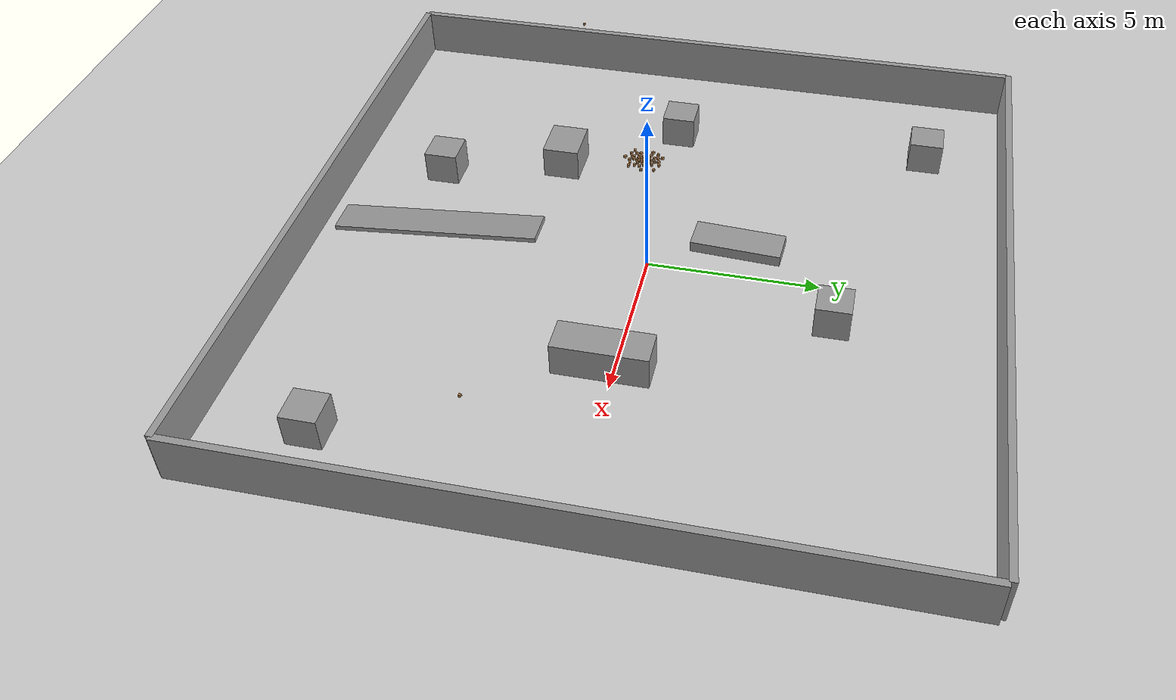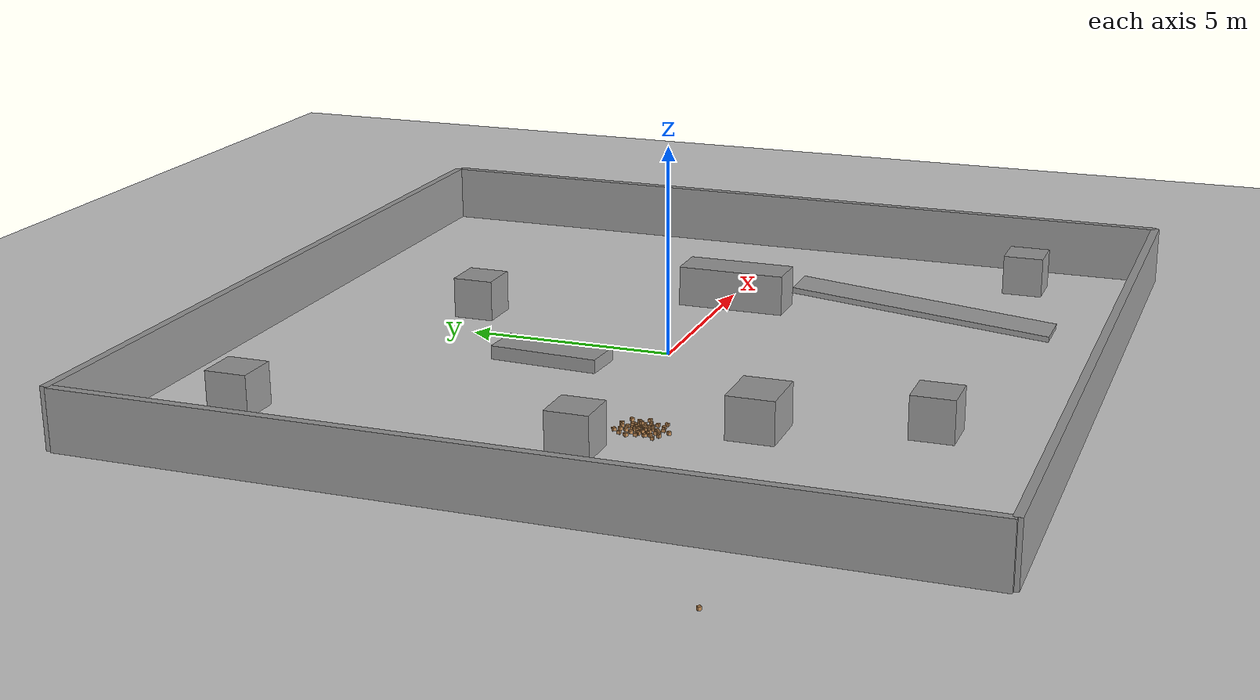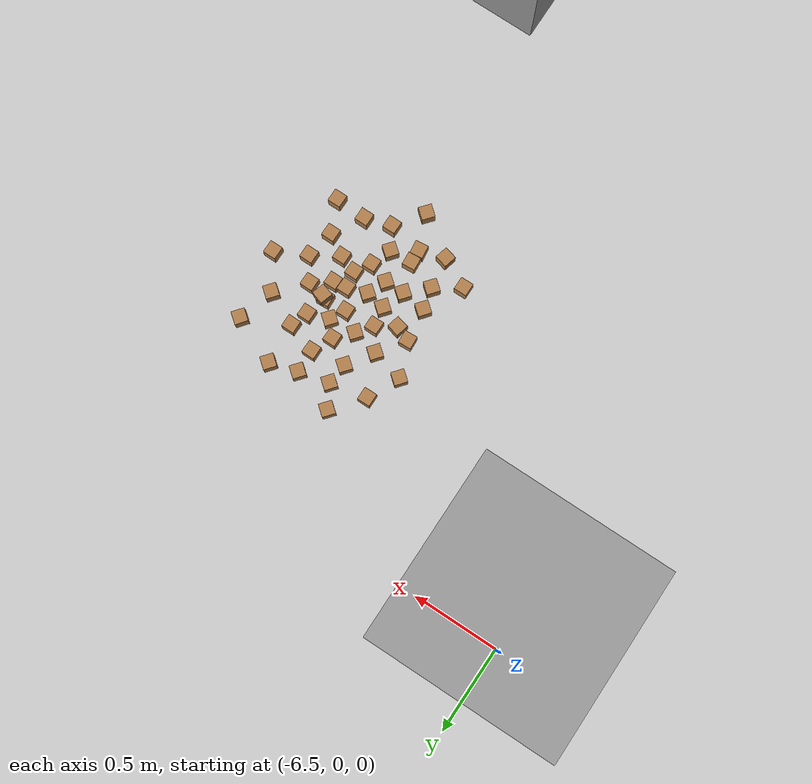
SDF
<sdf version="1.6">
 <world name="default">
  <light name="sun" type="directional">
   <cast_shadows>0</cast_shadows>
   <pose>0 0 10 0 -0 0</pose>
   <diffuse>0.8 0.8 0.8 1</diffuse>
   <specular>0.1 0.1 0.1 1</specular>
   <attenuation>
    <range>1000</range>
    <constant>0.9</constant>
    <linear>0.01</linear>
    <quadratic>0.001</quadratic>
   </attenuation>
   <direction>-0.5 0.5 -1</direction>
  </light>
  <model name="ground_plane">
   <static>1</static>
   <link name="link">
    <collision name="collision">
     <geometry><plane><normal>0 0 1</normal><size>100 100</size></plane></geometry>
     <surface><friction><ode><mu>100</mu><mu2>50</mu2></ode></friction></surface>
    </collision>
    <visual name="visual">
     <cast_shadows>0</cast_shadows>
     <geometry><plane><normal>0 0 1</normal><size>100 100</size></plane></geometry>
     <material>
      <script><uri>file://media/materials/scripts/gazebo.material</uri><name>Gazebo/Grey</name></script>
     </material>
    </visual>
   </link>
  </model>
  <gravity>0 0 -9.8</gravity>
  <magnetic_field>6e-06 2.3e-05 -4.2e-05</magnetic_field>
  <atmosphere type="adiabatic"/>
  <physics name="default_physics" default="0" type="ode">
   <max_step_size>0.001</max_step_size>
   <real_time_factor>1</real_time_factor>
   <real_time_update_rate>1000</real_time_update_rate>
  </physics>
  <scene><ambient>0.4 0.4 0.4 1</ambient><background>0.7 0.7 0.7 1</background><shadows>1</shadows></scene>
  <spherical_coordinates>
   <surface_model>EARTH_WGS84</surface_model>
   <latitude_deg>0</latitude_deg>
   <longitude_deg>0</longitude_deg>
   <elevation>0</elevation>
   <heading_deg>0</heading_deg>
  </spherical_coordinates>
  <model name="grey_wall_1">
   <link name="link">
    <inertial>
     <mass>1</mass>
     <inertia><ixx>1</ixx><ixy>0</ixy><ixz>0</ixz><iyy>1</iyy><iyz>0</iyz><izz>1</izz></inertia>
    </inertial>
    <visual name="visual">
     <cast_shadows>0</cast_shadows>
     <geometry><box><size>20 0.2 2.8</size></box></geometry>
     <material>
      <script>
       <uri>model://grey_wall/materials/scripts</uri>
       <uri>model://grey_wall/materials/textures</uri>
       <name>vrc/grey_wall</name>
      </script>
      <ambient>1 1 1 1</ambient>
      <diffuse>1 1 1 1</diffuse>
      <specular>0 0 0 1</specular>
      <emissive>0 0 0 1</emissive>
      <shader type="vertex"><normal_map>__default__</normal_map></shader>
     </material>
    </visual>
    <collision name="collision">
     <geometry><box><size>20 0.2 2.8</size></box></geometry>
     <surface>
      <friction>
       <ode><mu>1</mu><mu2>1</mu2><fdir1>0 0 0</fdir1><slip1>0</slip1><slip2>0</slip2></ode>
       <torsional>
        <coefficient>1</coefficient>
        <patch_radius>0</patch_radius>
        <surface_radius>0</surface_radius>
        <use_patch_radius>1</use_patch_radius>
        <ode><slip>0</slip></ode>
       </torsional>
      </friction>
      <bounce><restitution_coefficient>0</restitution_coefficient><threshold>1e+06</threshold></bounce>
      <contact>
       <collide_without_contact>0</collide_without_contact>
       <collide_without_contact_bitmask>1</collide_without_contact_bitmask>
       <collide_bitmask>1</collide_bitmask>
       <ode>
        <soft_cfm>0</soft_cfm>
        <soft_erp>0.2</soft_erp>
        <kp>1e+13</kp>
        <kd>1</kd>
        <max_vel>0.01</max_vel>
        <min_depth>0</min_depth>
       </ode>
       <bullet>
        <split_impulse>1</split_impulse>
        <split_impulse_penetration_threshold>-0.01</split_impulse_penetration_threshold>
        <soft_cfm>0</soft_cfm>
        <soft_erp>0.2</soft_erp>
        <kp>1e+13</kp>
        <kd>1</kd>
       </bullet>
      </contact>
     </surface>
    </collision>
   </link>
   <static>1</static>
   <pose>-0.041356 10.0529 3.5e-05 0 -0 0</pose>
  </model>
  <model name="grey_wall_2">
   <link name="link">
    <inertial>
     <mass>1</mass>
     <inertia><ixx>1</ixx><ixy>0</ixy><ixz>0</ixz><iyy>1</iyy><iyz>0</iyz><izz>1</izz></inertia>
    </inertial>
    <visual name="visual">
     <cast_shadows>0</cast_shadows>
     <geometry><box><size>20 0.2 2.8</size></box></geometry>
     <material>
      <script>
       <uri>model://grey_wall/materials/scripts</uri>
       <uri>model://grey_wall/materials/textures</uri>
       <name>vrc/grey_wall</name>
      </script>
      <ambient>1 1 1 1</ambient>
      <diffuse>1 1 1 1</diffuse>
      <specular>0 0 0 1</specular>
      <emissive>0 0 0 1</emissive>
      <shader type="vertex"><normal_map>__default__</normal_map></shader>
     </material>
    </visual>
    <collision name="collision">
     <geometry><box><size>20 0.2 2.8</size></box></geometry>
     <surface>
      <friction>
       <ode><mu>1</mu><mu2>1</mu2><fdir1>0 0 0</fdir1><slip1>0</slip1><slip2>0</slip2></ode>
       <torsional>
        <coefficient>1</coefficient>
        <patch_radius>0</patch_radius>
        <surface_radius>0</surface_radius>
        <use_patch_radius>1</use_patch_radius>
        <ode><slip>0</slip></ode>
       </torsional>
      </friction>
      <bounce><restitution_coefficient>0</restitution_coefficient><threshold>1e+06</threshold></bounce>
      <contact>
       <collide_without_contact>0</collide_without_contact>
       <collide_without_contact_bitmask>1</collide_without_contact_bitmask>
       <collide_bitmask>1</collide_bitmask>
       <ode>
        <soft_cfm>0</soft_cfm>
        <soft_erp>0.2</soft_erp>
        <kp>1e+13</kp>
        <kd>1</kd>
        <max_vel>0.01</max_vel>
        <min_depth>0</min_depth>
       </ode>
       <bullet>
        <split_impulse>1</split_impulse>
        <split_impulse_penetration_threshold>-0.01</split_impulse_penetration_threshold>
        <soft_cfm>0</soft_cfm>
        <soft_erp>0.2</soft_erp>
        <kp>1e+13</kp>
        <kd>1</kd>
       </bullet>
      </contact>
     </surface>
    </collision>
   </link>
   <static>1</static>
   <pose>0 -10 0 0 -0 0</pose>
  </model>
  <model name="grey_wall_3">
   <link name="link">
    <inertial>
     <mass>1</mass>
     <inertia><ixx>1</ixx><ixy>0</ixy><ixz>0</ixz><iyy>1</iyy><iyz>0</iyz><izz>1</izz></inertia>
    </inertial>
    <visual name="visual">
     <cast_shadows>0</cast_shadows>
     <geometry><box><size>20 0.2 2.8</size></box></geometry>
     <material>
      <script>
       <uri>model://grey_wall/materials/scripts</uri>
       <uri>model://grey_wall/materials/textures</uri>
       <name>vrc/grey_wall</name>
      </script>
      <ambient>1 1 1 1</ambient>
      <diffuse>1 1 1 1</diffuse>
      <specular>0 0 0 1</specular>
      <emissive>0 0 0 1</emissive>
      <shader type="vertex"><normal_map>__default__</normal_map></shader>
     </material>
    </visual>
    <collision name="collision">
     <geometry><box><size>20 0.2 2.8</size></box></geometry>
     <surface>
      <friction>
       <ode><mu>1</mu><mu2>1</mu2><fdir1>0 0 0</fdir1><slip1>0</slip1><slip2>0</slip2></ode>
       <torsional>
        <coefficient>1</coefficient>
        <patch_radius>0</patch_radius>
        <surface_radius>0</surface_radius>
        <use_patch_radius>1</use_patch_radius>
        <ode><slip>0</slip></ode>
       </torsional>
      </friction>
      <bounce><restitution_coefficient>0</restitution_coefficient><threshold>1e+06</threshold></bounce>
      <contact>
       <collide_without_contact>0</collide_without_contact>
       <collide_without_contact_bitmask>1</collide_without_contact_bitmask>
       <collide_bitmask>1</collide_bitmask>
       <ode>
        <soft_cfm>0</soft_cfm>
        <soft_erp>0.2</soft_erp>
        <kp>1e+13</kp>
        <kd>1</kd>
        <max_vel>0.01</max_vel>
        <min_depth>0</min_depth>
       </ode>
       <bullet>
        <split_impulse>1</split_impulse>
        <split_impulse_penetration_threshold>-0.01</split_impulse_penetration_threshold>
        <soft_cfm>0</soft_cfm>
        <soft_erp>0.2</soft_erp>
        <kp>1e+13</kp>
        <kd>1</kd>
       </bullet>
      </contact>
     </surface>
    </collision>
   </link>
   <static>1</static>
   <pose>-10 0 0 0 0 -1.5708</pose>
  </model>
  <model name="grey_wall_4">
   <link name="link">
    <inertial>
     <mass>1</mass>
     <inertia><ixx>1</ixx><ixy>0</ixy><ixz>0</ixz><iyy>1</iyy><iyz>0</iyz><izz>1</izz></inertia>
    </inertial>
    <visual name="visual">
     <cast_shadows>0</cast_shadows>
     <geometry><box><size>20 0.2 2.8</size></box></geometry>
     <material>
      <script>
       <uri>model://grey_wall/materials/scripts</uri>
       <uri>model://grey_wall/materials/textures</uri>
       <name>vrc/grey_wall</name>
      </script>
      <ambient>1 1 1 1</ambient>
      <diffuse>1 1 1 1</diffuse>
      <specular>0 0 0 1</specular>
      <emissive>0 0 0 1</emissive>
      <shader type="vertex"><normal_map>__default__</normal_map></shader>
     </material>
    </visual>
    <collision name="collision">
     <geometry><box><size>20 0.2 2.8</size></box></geometry>
     <surface>
      <friction>
       <ode><mu>1</mu><mu2>1</mu2><fdir1>0 0 0</fdir1><slip1>0</slip1><slip2>0</slip2></ode>
       <torsional>
        <coefficient>1</coefficient>
        <patch_radius>0</patch_radius>
        <surface_radius>0</surface_radius>
        <use_patch_radius>1</use_patch_radius>
        <ode><slip>0</slip></ode>
       </torsional>
      </friction>
      <bounce><restitution_coefficient>0</restitution_coefficient><threshold>1e+06</threshold></bounce>
      <contact>
       <collide_without_contact>0</collide_without_contact>
       <collide_without_contact_bitmask>1</collide_without_contact_bitmask>
       <collide_bitmask>1</collide_bitmask>
       <ode>
        <soft_cfm>0</soft_cfm>
        <soft_erp>0.2</soft_erp>
        <kp>1e+13</kp>
        <kd>1</kd>
        <max_vel>0.01</max_vel>
        <min_depth>0</min_depth>
       </ode>
       <bullet>
        <split_impulse>1</split_impulse>
        <split_impulse_penetration_threshold>-0.01</split_impulse_penetration_threshold>
        <soft_cfm>0</soft_cfm>
        <soft_erp>0.2</soft_erp>
        <kp>1e+13</kp>
        <kd>1</kd>
       </bullet>
      </contact>
     </surface>
    </collision>
   </link>
   <static>1</static>
   <pose>10 0 0 0 -0 1.5708</pose>
  </model>
  <model name="unit_box_0">
   <pose>-1.25916 2.45741 0.164114 -1e-06 8e-06 -0.059127</pose>
   <link name="link">
    <inertial>
     <mass>1</mass>
     <inertia>
      <ixx>0.166667</ixx>
      <ixy>0</ixy>
      <ixz>0</ixz>
      <iyy>0.166667</iyy>
      <iyz>0</iyz>
      <izz>0.166667</izz>
     </inertia>
    </inertial>
    <collision name="collision"><geometry><box><size>1 2.67 0.328237</size></box></geometry></collision>
    <visual name="visual">
     <geometry><box><size>1 2.67 0.328237</size></box></geometry>
     <material>
      <script><name>Gazebo/Grey</name><uri>file://media/materials/scripts/gazebo.material</uri></script>
     </material>
    </visual>
   </link>
  </model>
  <model name="unit_box_2">
   <pose>4.2885 -0.295508 0.499904 7.2e-05 -0 0</pose>
   <link name="link">
    <inertial>
     <mass>1</mass>
     <inertia>
      <ixx>0.166667</ixx>
      <ixy>0</ixy>
      <ixz>0</ixz>
      <iyy>0.166667</iyy>
      <iyz>0</iyz>
      <izz>0.166667</izz>
     </inertia>
    </inertial>
    <collision name="collision"><geometry><box><size>1 2.6886 1</size></box></geometry></collision>
    <visual name="visual">
     <geometry><box><size>1 2.6886 1</size></box></geometry>
     <material>
      <script><name>Gazebo/Grey</name><uri>file://media/materials/scripts/gazebo.material</uri></script>
     </material>
    </visual>
   </link>
  </model>
  <model name="unit_box_3">
   <pose>1.08261 -5.81184 1.44554 0.091408 -3e-06 -0.000371</pose>
   <link name="unit_box_3::unit_box_3::unit_box_3::unit_box_3::unit_box_3::link">
    <inertial>
     <mass>1</mass>
     <inertia>
      <ixx>0.166667</ixx>
      <ixy>0</ixy>
      <ixz>0</ixz>
      <iyy>0.166667</iyy>
      <iyz>0</iyz>
      <izz>0.166667</izz>
     </inertia>
    </inertial>
    <collision name="collision"><geometry><box><size>1 5.97463 0.129379</size></box></geometry></collision>
    <visual name="visual">
     <geometry><box><size>1 5.97463 0.129379</size></box></geometry>
     <material>
      <script><name>Gazebo/Grey</name><uri>file://media/materials/scripts/gazebo.material</uri></script>
     </material>
    </visual>
    <gravity>0</gravity>
   </link>
  </model>
  <model name="unit_box_4">
   <pose>-4.16236 -3.50219 0.5 0 -0 2e-06</pose>
   <link name="link">
    <inertial>
     <mass>1</mass>
     <inertia>
      <ixx>0.166667</ixx>
      <ixy>0</ixy>
      <ixz>0</ixz>
      <iyy>0.166667</iyy>
      <iyz>0</iyz>
      <izz>0.166667</izz>
     </inertia>
    </inertial>
    <collision name="collision"><geometry><box><size>1.32862 1.10201 1</size></box></geometry></collision>
    <visual name="visual">
     <geometry><box><size>1.32862 1.10201 1</size></box></geometry>
     <material>
      <script><name>Gazebo/Grey</name><uri>file://media/materials/scripts/gazebo.material</uri></script>
     </material>
    </visual>
   </link>
  </model>
  <model name="unit_box_5">
   <pose>-6.58812 7.62434 0.5 0 -0 0</pose>
   <link name="link">
    <inertial>
     <mass>1</mass>
     <inertia>
      <ixx>0.166667</ixx>
      <ixy>0</ixy>
      <ixz>0</ixz>
      <iyy>0.166667</iyy>
      <iyz>0</iyz>
      <izz>0.166667</izz>
     </inertia>
    </inertial>
    <collision name="collision"><geometry><box><size>1 1 1</size></box></geometry></collision>
    <visual name="visual">
     <geometry><box><size>1 1 1</size></box></geometry>
     <material>
      <script><name>Gazebo/Grey</name><uri>file://media/materials/scripts/gazebo.material</uri></script>
     </material>
    </visual>
   </link>
  </model>
  <model name="unit_box_7">
   <pose>1.47283 5.49709 0.5 0 -0 0</pose>
   <link name="link">
    <inertial>
     <mass>1</mass>
     <inertia>
      <ixx>0.166667</ixx>
      <ixy>0</ixy>
      <ixz>0</ixz>
      <iyy>0.166667</iyy>
      <iyz>0</iyz>
      <izz>0.166667</izz>
     </inertia>
    </inertial>
    <collision name="collision"><geometry><box><size>1 1 1</size></box></geometry></collision>
    <visual name="visual">
     <geometry><box><size>1 1 1</size></box></geometry>
     <material>
      <script><name>Gazebo/Grey</name><uri>file://media/materials/scripts/gazebo.material</uri></script>
     </material>
    </visual>
   </link>
  </model>
  <model name="unit_box_8">
   <pose>8 -7 0.5 0 -0 0</pose>
   <link name="link">
    <inertial>
     <mass>1</mass>
     <inertia>
      <ixx>0.166667</ixx>
      <ixy>0</ixy>
      <ixz>0</ixz>
      <iyy>0.166667</iyy>
      <iyz>0</iyz>
      <izz>0.166667</izz>
     </inertia>
    </inertial>
    <collision name="collision"><geometry><box><size>1 1 1</size></box></geometry></collision>
    <visual name="visual">
     <geometry><box><size>1 1 1</size></box></geometry>
     <material>
      <script><name>Gazebo/Grey</name><uri>file://media/materials/scripts/gazebo.material</uri></script>
     </material>
    </visual>
   </link>
  </model>
  <model name="unit_box_9">
   <pose>-3.0093 -7.07426 0.5 0 -0 0</pose>
   <link name="link">
    <inertial>
     <mass>1</mass>
     <inertia>
      <ixx>0.166667</ixx>
      <ixy>0</ixy>
      <ixz>0</ixz>
      <iyy>0.166667</iyy>
      <iyz>0</iyz>
      <izz>0.166667</izz>
     </inertia>
    </inertial>
    <collision name="collision"><geometry><box><size>1 1 1</size></box></geometry></collision>
    <visual name="visual">
     <geometry><box><size>1 1 1</size></box></geometry>
     <material>
      <script><name>Gazebo/Grey</name><uri>file://media/materials/scripts/gazebo.material</uri></script>
     </material>
    </visual>
   </link>
  </model>
  <model name="unit_box_10">
   <pose>-6.40752 -0.224773 0.5 0 -0 0</pose>
   <link name="link">
    <inertial>
     <mass>1</mass>
     <inertia>
      <ixx>0.166667</ixx>
      <ixy>0</ixy>
      <ixz>0</ixz>
      <iyy>0.166667</iyy>
      <iyz>0</iyz>
      <izz>0.166667</izz>
     </inertia>
    </inertial>
    <collision name="collision"><geometry><box><size>1 1 1</size></box></geometry></collision>
    <visual name="visual">
     <geometry><box><size>1 1 1</size></box></geometry>
     <material>
      <script><name>Gazebo/Grey</name><uri>file://media/materials/scripts/gazebo.material</uri></script>
     </material>
    </visual>
   </link>
  </model>
  <model name="wood_cube_7_5cm">
   <link name="link">
    <pose>0 0 0.0375 0 -0 0</pose>
    <inertial>
     <mass>0.2249</mass>
     <inertia>
      <ixx>0.000210844</ixx>
      <ixy>0</ixy>
      <ixz>0</ixz>
      <iyy>0.000210844</iyy>
      <iyz>0</iyz>
      <izz>0.000210844</izz>
     </inertia>
    </inertial>
    <collision name="collision">
     <geometry><box><size>0.075 0.075 0.075</size></box></geometry>
     <surface>
      <contact>
       <poissons_ratio>0.347</poissons_ratio>
       <elastic_modulus>8.8e+09</elastic_modulus>
       <ode><kp>100000</kp><kd>100</kd><max_vel>100</max_vel><min_depth>0.001</min_depth></ode>
      </contact>
      <friction>
       <torsional>
        <coefficient>1</coefficient>
        <use_patch_radius>0</use_patch_radius>
        <surface_radius>0.01</surface_radius>
       </torsional>
      </friction>
     </surface>
    </collision>
    <visual name="visual">
     <geometry><box><size>0.075 0.075 0.075</size></box></geometry>
     <material>
      <script><uri>file://media/materials/scripts/gazebo.material</uri><name>Gazebo/Wood</name></script>
     </material>
    </visual>
   </link>
   <pose>-5.02546 -1.07869 -0.001005 0 -0 1.2e-05</pose>
  </model>
  <model name="wood_cube_7_5cm_clone">
   <link name="link">
    <pose>0 0 0.0375 0 -0 0</pose>
    <inertial>
     <mass>0.2249</mass>
     <inertia>
      <ixx>0.000210844</ixx>
      <ixy>0</ixy>
      <ixz>0</ixz>
      <iyy>0.000210844</iyy>
      <iyz>0</iyz>
      <izz>0.000210844</izz>
     </inertia>
    </inertial>
    <collision name="collision">
     <geometry><box><size>0.075 0.075 0.075</size></box></geometry>
     <surface>
      <contact>
       <poissons_ratio>0.347</poissons_ratio>
       <elastic_modulus>8.8e+09</elastic_modulus>
       <ode><kp>100000</kp><kd>100</kd><max_vel>100</max_vel><min_depth>0.001</min_depth></ode>
      </contact>
      <friction>
       <torsional>
        <coefficient>1</coefficient>
        <use_patch_radius>0</use_patch_radius>
        <surface_radius>0.01</surface_radius>
       </torsional>
      </friction>
     </surface>
    </collision>
    <visual name="visual">
     <geometry><box><size>0.075 0.075 0.075</size></box></geometry>
     <material>
      <script><uri>file://media/materials/scripts/gazebo.material</uri><name>Gazebo/Wood</name></script>
     </material>
    </visual>
   </link>
   <pose>-4.99781 -1.55978 -0.001005 0 -0 0.11602</pose>
  </model>
  <model name="wood_cube_7_5cm_clone_0">
   <link name="link">
    <pose>0 0 0.0375 0 -0 0</pose>
    <inertial>
     <mass>0.2249</mass>
     <inertia>
      <ixx>0.000210844</ixx>
      <ixy>0</ixy>
      <ixz>0</ixz>
      <iyy>0.000210844</iyy>
      <iyz>0</iyz>
      <izz>0.000210844</izz>
     </inertia>
    </inertial>
    <collision name="collision">
     <geometry><box><size>0.075 0.075 0.075</size></box></geometry>
     <surface>
      <contact>
       <poissons_ratio>0.347</poissons_ratio>
       <elastic_modulus>8.8e+09</elastic_modulus>
       <ode><kp>100000</kp><kd>100</kd><max_vel>100</max_vel><min_depth>0.001</min_depth></ode>
      </contact>
      <friction>
       <torsional>
        <coefficient>1</coefficient>
        <use_patch_radius>0</use_patch_radius>
        <surface_radius>0.01</surface_radius>
       </torsional>
      </friction>
     </surface>
    </collision>
    <visual name="visual">
     <geometry><box><size>0.075 0.075 0.075</size></box></geometry>
     <material>
      <script><uri>file://media/materials/scripts/gazebo.material</uri><name>Gazebo/Wood</name></script>
     </material>
    </visual>
   </link>
   <pose>-4.54749 -1.37644 -0.001005 0 -0 0</pose>
  </model>
  <model name="wood_cube_7_5cm_clone_1">
   <link name="link">
    <pose>0 0 0.0375 0 -0 0</pose>
    <inertial>
     <mass>0.2249</mass>
     <inertia>
      <ixx>0.000210844</ixx>
      <ixy>0</ixy>
      <ixz>0</ixz>
      <iyy>0.000210844</iyy>
      <iyz>0</iyz>
      <izz>0.000210844</izz>
     </inertia>
    </inertial>
    <collision name="collision">
     <geometry><box><size>0.075 0.075 0.075</size></box></geometry>
     <surface>
      <contact>
       <poissons_ratio>0.347</poissons_ratio>
       <elastic_modulus>8.8e+09</elastic_modulus>
       <ode><kp>100000</kp><kd>100</kd><max_vel>100</max_vel><min_depth>0.001</min_depth></ode>
      </contact>
      <friction>
       <torsional>
        <coefficient>1</coefficient>
        <use_patch_radius>0</use_patch_radius>
        <surface_radius>0.01</surface_radius>
       </torsional>
      </friction>
     </surface>
    </collision>
    <visual name="visual">
     <geometry><box><size>0.075 0.075 0.075</size></box></geometry>
     <material>
      <script><uri>file://media/materials/scripts/gazebo.material</uri><name>Gazebo/Wood</name></script>
     </material>
    </visual>
   </link>
   <pose>-5.00216 -1.44497 0.036495 1.5708 -0 0.066024</pose>
  </model>
  <model name="wood_cube_7_5cm_clone_2">
   <link name="link">
    <pose>0 0 0.0375 0 -0 0</pose>
    <inertial>
     <mass>0.2249</mass>
     <inertia>
      <ixx>0.000210844</ixx>
      <ixy>0</ixy>
      <ixz>0</ixz>
      <iyy>0.000210844</iyy>
      <iyz>0</iyz>
      <izz>0.000210844</izz>
     </inertia>
    </inertial>
    <collision name="collision">
     <geometry><box><size>0.075 0.075 0.075</size></box></geometry>
     <surface>
      <contact>
       <poissons_ratio>0.347</poissons_ratio>
       <elastic_modulus>8.8e+09</elastic_modulus>
       <ode><kp>100000</kp><kd>100</kd><max_vel>100</max_vel><min_depth>0.001</min_depth></ode>
      </contact>
      <friction>
       <torsional>
        <coefficient>1</coefficient>
        <use_patch_radius>0</use_patch_radius>
        <surface_radius>0.01</surface_radius>
       </torsional>
      </friction>
     </surface>
    </collision>
    <visual name="visual">
     <geometry><box><size>0.075 0.075 0.075</size></box></geometry>
     <material>
      <script><uri>file://media/materials/scripts/gazebo.material</uri><name>Gazebo/Wood</name></script>
     </material>
    </visual>
   </link>
   <pose>-4.76924 -1.26859 -0.001005 0 -0 0</pose>
  </model>
  <model name="wood_cube_7_5cm_clone_3">
   <link name="link">
    <pose>0 0 0.0375 0 -0 0</pose>
    <inertial>
     <mass>0.2249</mass>
     <inertia>
      <ixx>0.000210844</ixx>
      <ixy>0</ixy>
      <ixz>0</ixz>
      <iyy>0.000210844</iyy>
      <iyz>0</iyz>
      <izz>0.000210844</izz>
     </inertia>
    </inertial>
    <collision name="collision">
     <geometry><box><size>0.075 0.075 0.075</size></box></geometry>
     <surface>
      <contact>
       <poissons_ratio>0.347</poissons_ratio>
       <elastic_modulus>8.8e+09</elastic_modulus>
       <ode><kp>100000</kp><kd>100</kd><max_vel>100</max_vel><min_depth>0.001</min_depth></ode>
      </contact>
      <friction>
       <torsional>
        <coefficient>1</coefficient>
        <use_patch_radius>0</use_patch_radius>
        <surface_radius>0.01</surface_radius>
       </torsional>
      </friction>
     </surface>
    </collision>
    <visual name="visual">
     <geometry><box><size>0.075 0.075 0.075</size></box></geometry>
     <material>
      <script><uri>file://media/materials/scripts/gazebo.material</uri><name>Gazebo/Wood</name></script>
     </material>
    </visual>
   </link>
   <pose>-12.573 -5.05385 0.036495 1.5708 -0 -2.39587</pose>
  </model>
  <model name="wood_cube_7_5cm_clone_4">
   <link name="link">
    <pose>0 0 0.0375 0 -0 0</pose>
    <inertial>
     <mass>0.2249</mass>
     <inertia>
      <ixx>0.000210844</ixx>
      <ixy>0</ixy>
      <ixz>0</ixz>
      <iyy>0.000210844</iyy>
      <iyz>0</iyz>
      <izz>0.000210844</izz>
     </inertia>
    </inertial>
    <collision name="collision">
     <geometry><box><size>0.075 0.075 0.075</size></box></geometry>
     <surface>
      <contact>
       <poissons_ratio>0.347</poissons_ratio>
       <elastic_modulus>8.8e+09</elastic_modulus>
       <ode><kp>100000</kp><kd>100</kd><max_vel>100</max_vel><min_depth>0.001</min_depth></ode>
      </contact>
      <friction>
       <torsional>
        <coefficient>1</coefficient>
        <use_patch_radius>0</use_patch_radius>
        <surface_radius>0.01</surface_radius>
       </torsional>
      </friction>
     </surface>
    </collision>
    <visual name="visual">
     <geometry><box><size>0.075 0.075 0.075</size></box></geometry>
     <material>
      <script><uri>file://media/materials/scripts/gazebo.material</uri><name>Gazebo/Wood</name></script>
     </material>
    </visual>
   </link>
   <pose>-4.72319 -1.05993 -0.001011 -1.3e-05 3.7e-05 0.048566</pose>
  </model>
  <model name="wood_cube_7_5cm_clone_5">
   <link name="link">
    <pose>0 0 0.0375 0 -0 0</pose>
    <inertial>
     <mass>0.2249</mass>
     <inertia>
      <ixx>0.000210844</ixx>
      <ixy>0</ixy>
      <ixz>0</ixz>
      <iyy>0.000210844</iyy>
      <iyz>0</iyz>
      <izz>0.000210844</izz>
     </inertia>
    </inertial>
    <collision name="collision">
     <geometry><box><size>0.075 0.075 0.075</size></box></geometry>
     <surface>
      <contact>
       <poissons_ratio>0.347</poissons_ratio>
       <elastic_modulus>8.8e+09</elastic_modulus>
       <ode><kp>100000</kp><kd>100</kd><max_vel>100</max_vel><min_depth>0.001</min_depth></ode>
      </contact>
      <friction>
       <torsional>
        <coefficient>1</coefficient>
        <use_patch_radius>0</use_patch_radius>
        <surface_radius>0.01</surface_radius>
       </torsional>
      </friction>
     </surface>
    </collision>
    <visual name="visual">
     <geometry><box><size>0.075 0.075 0.075</size></box></geometry>
     <material>
      <script><uri>file://media/materials/scripts/gazebo.material</uri><name>Gazebo/Wood</name></script>
     </material>
    </visual>
   </link>
   <pose>-4.78458 -1.17206 -0.001005 0 -0 5e-05</pose>
  </model>
  <model name="wood_cube_7_5cm_clone_6">
   <link name="link">
    <pose>0 0 0.0375 0 -0 0</pose>
    <inertial>
     <mass>0.2249</mass>
     <inertia>
      <ixx>0.000210844</ixx>
      <ixy>0</ixy>
      <ixz>0</ixz>
      <iyy>0.000210844</iyy>
      <iyz>0</iyz>
      <izz>0.000210844</izz>
     </inertia>
    </inertial>
    <collision name="collision">
     <geometry><box><size>0.075 0.075 0.075</size></box></geometry>
     <surface>
      <contact>
       <poissons_ratio>0.347</poissons_ratio>
       <elastic_modulus>8.8e+09</elastic_modulus>
       <ode><kp>100000</kp><kd>100</kd><max_vel>100</max_vel><min_depth>0.001</min_depth></ode>
      </contact>
      <friction>
       <torsional>
        <coefficient>1</coefficient>
        <use_patch_radius>0</use_patch_radius>
        <surface_radius>0.01</surface_radius>
       </torsional>
      </friction>
     </surface>
    </collision>
    <visual name="visual">
     <geometry><box><size>0.075 0.075 0.075</size></box></geometry>
     <material>
      <script><uri>file://media/materials/scripts/gazebo.material</uri><name>Gazebo/Wood</name></script>
     </material>
    </visual>
   </link>
   <pose>-4.66696 -1.30348 -0.001005 0 -0 0</pose>
  </model>
  <model name="wood_cube_7_5cm_clone_7">
   <link name="link">
    <pose>0 0 0.0375 0 -0 0</pose>
    <inertial>
     <mass>0.2249</mass>
     <inertia>
      <ixx>0.000210844</ixx>
      <ixy>0</ixy>
      <ixz>0</ixz>
      <iyy>0.000210844</iyy>
      <iyz>0</iyz>
      <izz>0.000210844</izz>
     </inertia>
    </inertial>
    <collision name="collision">
     <geometry><box><size>0.075 0.075 0.075</size></box></geometry>
     <surface>
      <contact>
       <poissons_ratio>0.347</poissons_ratio>
       <elastic_modulus>8.8e+09</elastic_modulus>
       <ode><kp>100000</kp><kd>100</kd><max_vel>100</max_vel><min_depth>0.001</min_depth></ode>
      </contact>
      <friction>
       <torsional>
        <coefficient>1</coefficient>
        <use_patch_radius>0</use_patch_radius>
        <surface_radius>0.01</surface_radius>
       </torsional>
      </friction>
     </surface>
    </collision>
    <visual name="visual">
     <geometry><box><size>0.075 0.075 0.075</size></box></geometry>
     <material>
      <script><uri>file://media/materials/scripts/gazebo.material</uri><name>Gazebo/Wood</name></script>
     </material>
    </visual>
   </link>
   <pose>-4.82543 -1.35696 -0.001005 0 -0 0</pose>
  </model>
  <model name="wood_cube_7_5cm_clone_8">
   <link name="link">
    <pose>0 0 0.0375 0 -0 0</pose>
    <inertial>
     <mass>0.2249</mass>
     <inertia>
      <ixx>0.000210844</ixx>
      <ixy>0</ixy>
      <ixz>0</ixz>
      <iyy>0.000210844</iyy>
      <iyz>0</iyz>
      <izz>0.000210844</izz>
     </inertia>
    </inertial>
    <collision name="collision">
     <geometry><box><size>0.075 0.075 0.075</size></box></geometry>
     <surface>
      <contact>
       <poissons_ratio>0.347</poissons_ratio>
       <elastic_modulus>8.8e+09</elastic_modulus>
       <ode><kp>100000</kp><kd>100</kd><max_vel>100</max_vel><min_depth>0.001</min_depth></ode>
      </contact>
      <friction>
       <torsional>
        <coefficient>1</coefficient>
        <use_patch_radius>0</use_patch_radius>
        <surface_radius>0.01</surface_radius>
       </torsional>
      </friction>
     </surface>
    </collision>
    <visual name="visual">
     <geometry><box><size>0.075 0.075 0.075</size></box></geometry>
     <material>
      <script><uri>file://media/materials/scripts/gazebo.material</uri><name>Gazebo/Wood</name></script>
     </material>
    </visual>
   </link>
   <pose>-4.91761 -1.7568 -0.001005 -0 -0 -2.27099</pose>
  </model>
  <model name="wood_cube_7_5cm_clone_9">
   <link name="link">
    <pose>0 0 0.0375 0 -0 0</pose>
    <inertial>
     <mass>0.2249</mass>
     <inertia>
      <ixx>0.000210844</ixx>
      <ixy>0</ixy>
      <ixz>0</ixz>
      <iyy>0.000210844</iyy>
      <iyz>0</iyz>
      <izz>0.000210844</izz>
     </inertia>
    </inertial>
    <collision name="collision">
     <geometry><box><size>0.075 0.075 0.075</size></box></geometry>
     <surface>
      <contact>
       <poissons_ratio>0.347</poissons_ratio>
       <elastic_modulus>8.8e+09</elastic_modulus>
       <ode><kp>100000</kp><kd>100</kd><max_vel>100</max_vel><min_depth>0.001</min_depth></ode>
      </contact>
      <friction>
       <torsional>
        <coefficient>1</coefficient>
        <use_patch_radius>0</use_patch_radius>
        <surface_radius>0.01</surface_radius>
       </torsional>
      </friction>
     </surface>
    </collision>
    <visual name="visual">
     <geometry><box><size>0.075 0.075 0.075</size></box></geometry>
     <material>
      <script><uri>file://media/materials/scripts/gazebo.material</uri><name>Gazebo/Wood</name></script>
     </material>
    </visual>
   </link>
   <pose>-4.46926 -1.55552 -0.001005 0 -0 0</pose>
  </model>
  <model name="wood_cube_7_5cm_clone_10">
   <link name="link">
    <pose>0 0 0.0375 0 -0 0</pose>
    <inertial>
     <mass>0.2249</mass>
     <inertia>
      <ixx>0.000210844</ixx>
      <ixy>0</ixy>
      <ixz>0</ixz>
      <iyy>0.000210844</iyy>
      <iyz>0</iyz>
      <izz>0.000210844</izz>
     </inertia>
    </inertial>
    <collision name="collision">
     <geometry><box><size>0.075 0.075 0.075</size></box></geometry>
     <surface>
      <contact>
       <poissons_ratio>0.347</poissons_ratio>
       <elastic_modulus>8.8e+09</elastic_modulus>
       <ode><kp>100000</kp><kd>100</kd><max_vel>100</max_vel><min_depth>0.001</min_depth></ode>
      </contact>
      <friction>
       <torsional>
        <coefficient>1</coefficient>
        <use_patch_radius>0</use_patch_radius>
        <surface_radius>0.01</surface_radius>
       </torsional>
      </friction>
     </surface>
    </collision>
    <visual name="visual">
     <geometry><box><size>0.075 0.075 0.075</size></box></geometry>
     <material>
      <script><uri>file://media/materials/scripts/gazebo.material</uri><name>Gazebo/Wood</name></script>
     </material>
    </visual>
   </link>
   <pose>-4.64924 -1.54846 -0.001005 0 -0 0</pose>
  </model>
  <model name="wood_cube_7_5cm_clone_11">
   <link name="link">
    <pose>0 0 0.0375 0 -0 0</pose>
    <inertial>
     <mass>0.2249</mass>
     <inertia>
      <ixx>0.000210844</ixx>
      <ixy>0</ixy>
      <ixz>0</ixz>
      <iyy>0.000210844</iyy>
      <iyz>0</iyz>
      <izz>0.000210844</izz>
     </inertia>
    </inertial>
    <collision name="collision">
     <geometry><box><size>0.075 0.075 0.075</size></box></geometry>
     <surface>
      <contact>
       <poissons_ratio>0.347</poissons_ratio>
       <elastic_modulus>8.8e+09</elastic_modulus>
       <ode><kp>100000</kp><kd>100</kd><max_vel>100</max_vel><min_depth>0.001</min_depth></ode>
      </contact>
      <friction>
       <torsional>
        <coefficient>1</coefficient>
        <use_patch_radius>0</use_patch_radius>
        <surface_radius>0.01</surface_radius>
       </torsional>
      </friction>
     </surface>
    </collision>
    <visual name="visual">
     <geometry><box><size>0.075 0.075 0.075</size></box></geometry>
     <material>
      <script><uri>file://media/materials/scripts/gazebo.material</uri><name>Gazebo/Wood</name></script>
     </material>
    </visual>
   </link>
   <pose>-4.33978 -1.12304 -0.001005 0 -0 0</pose>
  </model>
  <model name="wood_cube_7_5cm_clone_12">
   <link name="link">
    <pose>0 0 0.0375 0 -0 0</pose>
    <inertial>
     <mass>0.2249</mass>
     <inertia>
      <ixx>0.000210844</ixx>
      <ixy>0</ixy>
      <ixz>0</ixz>
      <iyy>0.000210844</iyy>
      <iyz>0</iyz>
      <izz>0.000210844</izz>
     </inertia>
    </inertial>
    <collision name="collision">
     <geometry><box><size>0.075 0.075 0.075</size></box></geometry>
     <surface>
      <contact>
       <poissons_ratio>0.347</poissons_ratio>
       <elastic_modulus>8.8e+09</elastic_modulus>
       <ode><kp>100000</kp><kd>100</kd><max_vel>100</max_vel><min_depth>0.001</min_depth></ode>
      </contact>
      <friction>
       <torsional>
        <coefficient>1</coefficient>
        <use_patch_radius>0</use_patch_radius>
        <surface_radius>0.01</surface_radius>
       </torsional>
      </friction>
     </surface>
    </collision>
    <visual name="visual">
     <geometry><box><size>0.075 0.075 0.075</size></box></geometry>
     <material>
      <script><uri>file://media/materials/scripts/gazebo.material</uri><name>Gazebo/Wood</name></script>
     </material>
    </visual>
   </link>
   <pose>-4.6518 -0.839595 -0.001005 0 -0 0</pose>
  </model>
  <model name="wood_cube_7_5cm_clone_14">
   <link name="link">
    <pose>0 0 0.0375 0 -0 0</pose>
    <inertial>
     <mass>0.2249</mass>
     <inertia>
      <ixx>0.000210844</ixx>
      <ixy>0</ixy>
      <ixz>0</ixz>
      <iyy>0.000210844</iyy>
      <iyz>0</iyz>
      <izz>0.000210844</izz>
     </inertia>
    </inertial>
    <collision name="collision">
     <geometry><box><size>0.075 0.075 0.075</size></box></geometry>
     <surface>
      <contact>
       <poissons_ratio>0.347</poissons_ratio>
       <elastic_modulus>8.8e+09</elastic_modulus>
       <ode><kp>100000</kp><kd>100</kd><max_vel>100</max_vel><min_depth>0.001</min_depth></ode>
      </contact>
      <friction>
       <torsional>
        <coefficient>1</coefficient>
        <use_patch_radius>0</use_patch_radius>
        <surface_radius>0.01</surface_radius>
       </torsional>
      </friction>
     </surface>
    </collision>
    <visual name="visual">
     <geometry><box><size>0.075 0.075 0.075</size></box></geometry>
     <material>
      <script><uri>file://media/materials/scripts/gazebo.material</uri><name>Gazebo/Wood</name></script>
     </material>
    </visual>
   </link>
   <pose>6.07733 -3.66885 0.036495 -1.5708 0 2.92546</pose>
  </model>
  <model name="wood_cube_7_5cm_clone_7_clone">
   <link name="link">
    <pose>0 0 0.0375 0 -0 0</pose>
    <inertial>
     <mass>0.2249</mass>
     <inertia>
      <ixx>0.000210844</ixx>
      <ixy>0</ixy>
      <ixz>0</ixz>
      <iyy>0.000210844</iyy>
      <iyz>0</iyz>
      <izz>0.000210844</izz>
     </inertia>
    </inertial>
    <collision name="collision">
     <geometry><box><size>0.075 0.075 0.075</size></box></geometry>
     <surface>
      <contact>
       <poissons_ratio>0.347</poissons_ratio>
       <elastic_modulus>8.8e+09</elastic_modulus>
       <ode><kp>100000</kp><kd>100</kd><max_vel>100</max_vel><min_depth>0.001</min_depth></ode>
      </contact>
      <friction>
       <torsional>
        <coefficient>1</coefficient>
        <use_patch_radius>0</use_patch_radius>
        <surface_radius>0.01</surface_radius>
       </torsional>
      </friction>
     </surface>
    </collision>
    <visual name="visual">
     <geometry><box><size>0.075 0.075 0.075</size></box></geometry>
     <material>
      <script><uri>file://media/materials/scripts/gazebo.material</uri><name>Gazebo/Wood</name></script>
     </material>
    </visual>
   </link>
   <pose>-4.74428 -1.1622 0.036495 3.141 1.57079 3.14159</pose>
  </model>
  <model name="wood_cube_7_5cm_clone_7_clone_0">
   <link name="link">
    <pose>0 0 0.0375 0 -0 0</pose>
    <inertial>
     <mass>0.2249</mass>
     <inertia>
      <ixx>0.000210844</ixx>
      <ixy>0</ixy>
      <ixz>0</ixz>
      <iyy>0.000210844</iyy>
      <iyz>0</iyz>
      <izz>0.000210844</izz>
     </inertia>
    </inertial>
    <collision name="collision">
     <geometry><box><size>0.075 0.075 0.075</size></box></geometry>
     <surface>
      <contact>
       <poissons_ratio>0.347</poissons_ratio>
       <elastic_modulus>8.8e+09</elastic_modulus>
       <ode><kp>100000</kp><kd>100</kd><max_vel>100</max_vel><min_depth>0.001</min_depth></ode>
      </contact>
      <friction>
       <torsional>
        <coefficient>1</coefficient>
        <use_patch_radius>0</use_patch_radius>
        <surface_radius>0.01</surface_radius>
       </torsional>
      </friction>
     </surface>
    </collision>
    <visual name="visual">
     <geometry><box><size>0.075 0.075 0.075</size></box></geometry>
     <material>
      <script><uri>file://media/materials/scripts/gazebo.material</uri><name>Gazebo/Wood</name></script>
     </material>
    </visual>
   </link>
   <pose>-4.87624 -0.899987 -0.001005 0 -0 0</pose>
  </model>
  <model name="wood_cube_7_5cm_clone_7_clone_1">
   <link name="link">
    <pose>0 0 0.0375 0 -0 0</pose>
    <inertial>
     <mass>0.2249</mass>
     <inertia>
      <ixx>0.000210844</ixx>
      <ixy>0</ixy>
      <ixz>0</ixz>
      <iyy>0.000210844</iyy>
      <iyz>0</iyz>
      <izz>0.000210844</izz>
     </inertia>
    </inertial>
    <collision name="collision">
     <geometry><box><size>0.075 0.075 0.075</size></box></geometry>
     <surface>
      <contact>
       <poissons_ratio>0.347</poissons_ratio>
       <elastic_modulus>8.8e+09</elastic_modulus>
       <ode><kp>100000</kp><kd>100</kd><max_vel>100</max_vel><min_depth>0.001</min_depth></ode>
      </contact>
      <friction>
       <torsional>
        <coefficient>1</coefficient>
        <use_patch_radius>0</use_patch_radius>
        <surface_radius>0.01</surface_radius>
       </torsional>
      </friction>
     </surface>
    </collision>
    <visual name="visual">
     <geometry><box><size>0.075 0.075 0.075</size></box></geometry>
     <material>
      <script><uri>file://media/materials/scripts/gazebo.material</uri><name>Gazebo/Wood</name></script>
     </material>
    </visual>
   </link>
   <pose>-5.11135 -0.959806 -0.001005 0 0 -0.685305</pose>
  </model>
  <model name="wood_cube_7_5cm_clone_7_clone_2">
   <link name="link">
    <pose>0 0 0.0375 0 -0 0</pose>
    <inertial>
     <mass>0.2249</mass>
     <inertia>
      <ixx>0.000210844</ixx>
      <ixy>0</ixy>
      <ixz>0</ixz>
      <iyy>0.000210844</iyy>
      <iyz>0</iyz>
      <izz>0.000210844</izz>
     </inertia>
    </inertial>
    <collision name="collision">
     <geometry><box><size>0.075 0.075 0.075</size></box></geometry>
     <surface>
      <contact>
       <poissons_ratio>0.347</poissons_ratio>
       <elastic_modulus>8.8e+09</elastic_modulus>
       <ode><kp>100000</kp><kd>100</kd><max_vel>100</max_vel><min_depth>0.001</min_depth></ode>
      </contact>
      <friction>
       <torsional>
        <coefficient>1</coefficient>
        <use_patch_radius>0</use_patch_radius>
        <surface_radius>0.01</surface_radius>
       </torsional>
      </friction>
     </surface>
    </collision>
    <visual name="visual">
     <geometry><box><size>0.075 0.075 0.075</size></box></geometry>
     <material>
      <script><uri>file://media/materials/scripts/gazebo.material</uri><name>Gazebo/Wood</name></script>
     </material>
    </visual>
   </link>
   <pose>-5.2109 -0.734076 -0.001005 0 -0 0</pose>
  </model>
  <model name="wood_cube_7_5cm_clone_7_clone_3">
   <link name="link">
    <pose>0 0 0.0375 0 -0 0</pose>
    <inertial>
     <mass>0.2249</mass>
     <inertia>
      <ixx>0.000210844</ixx>
      <ixy>0</ixy>
      <ixz>0</ixz>
      <iyy>0.000210844</iyy>
      <iyz>0</iyz>
      <izz>0.000210844</izz>
     </inertia>
    </inertial>
    <collision name="collision">
     <geometry><box><size>0.075 0.075 0.075</size></box></geometry>
     <surface>
      <contact>
       <poissons_ratio>0.347</poissons_ratio>
       <elastic_modulus>8.8e+09</elastic_modulus>
       <ode><kp>100000</kp><kd>100</kd><max_vel>100</max_vel><min_depth>0.001</min_depth></ode>
      </contact>
      <friction>
       <torsional>
        <coefficient>1</coefficient>
        <use_patch_radius>0</use_patch_radius>
        <surface_radius>0.01</surface_radius>
       </torsional>
      </friction>
     </surface>
    </collision>
    <visual name="visual">
     <geometry><box><size>0.075 0.075 0.075</size></box></geometry>
     <material>
      <script><uri>file://media/materials/scripts/gazebo.material</uri><name>Gazebo/Wood</name></script>
     </material>
    </visual>
   </link>
   <pose>-4.85182 -1.06434 -0.001005 0 -0 0</pose>
  </model>
  <model name="wood_cube_7_5cm_clone_7_clone_4">
   <link name="link">
    <pose>0 0 0.0375 0 -0 0</pose>
    <inertial>
     <mass>0.2249</mass>
     <inertia>
      <ixx>0.000210844</ixx>
      <ixy>0</ixy>
      <ixz>0</ixz>
      <iyy>0.000210844</iyy>
      <iyz>0</iyz>
      <izz>0.000210844</izz>
     </inertia>
    </inertial>
    <collision name="collision">
     <geometry><box><size>0.075 0.075 0.075</size></box></geometry>
     <surface>
      <contact>
       <poissons_ratio>0.347</poissons_ratio>
       <elastic_modulus>8.8e+09</elastic_modulus>
       <ode><kp>100000</kp><kd>100</kd><max_vel>100</max_vel><min_depth>0.001</min_depth></ode>
      </contact>
      <friction>
       <torsional>
        <coefficient>1</coefficient>
        <use_patch_radius>0</use_patch_radius>
        <surface_radius>0.01</surface_radius>
       </torsional>
      </friction>
     </surface>
    </collision>
    <visual name="visual">
     <geometry><box><size>0.075 0.075 0.075</size></box></geometry>
     <material>
      <script><uri>file://media/materials/scripts/gazebo.material</uri><name>Gazebo/Wood</name></script>
     </material>
    </visual>
   </link>
   <pose>-4.95967 -0.992197 -0.001005 0 -0 -0.692422</pose>
  </model>
  <model name="wood_cube_7_5cm_clone_7_clone_5">
   <link name="link">
    <pose>0 0 0.0375 0 -0 0</pose>
    <inertial>
     <mass>0.2249</mass>
     <inertia>
      <ixx>0.000210844</ixx>
      <ixy>0</ixy>
      <ixz>0</ixz>
      <iyy>0.000210844</iyy>
      <iyz>0</iyz>
      <izz>0.000210844</izz>
     </inertia>
    </inertial>
    <collision name="collision">
     <geometry><box><size>0.075 0.075 0.075</size></box></geometry>
     <surface>
      <contact>
       <poissons_ratio>0.347</poissons_ratio>
       <elastic_modulus>8.8e+09</elastic_modulus>
       <ode><kp>100000</kp><kd>100</kd><max_vel>100</max_vel><min_depth>0.001</min_depth></ode>
      </contact>
      <friction>
       <torsional>
        <coefficient>1</coefficient>
        <use_patch_radius>0</use_patch_radius>
        <surface_radius>0.01</surface_radius>
       </torsional>
      </friction>
     </surface>
    </collision>
    <visual name="visual">
     <geometry><box><size>0.075 0.075 0.075</size></box></geometry>
     <material>
      <script><uri>file://media/materials/scripts/gazebo.material</uri><name>Gazebo/Wood</name></script>
     </material>
    </visual>
   </link>
   <pose>-5.14408 -1.17949 0.036495 1.32422 -1.57079 3.14159</pose>
  </model>
  <model name="wood_cube_7_5cm_clone_7_clone_6">
   <link name="link">
    <pose>0 0 0.0375 0 -0 0</pose>
    <inertial>
     <mass>0.2249</mass>
     <inertia>
      <ixx>0.000210844</ixx>
      <ixy>0</ixy>
      <ixz>0</ixz>
      <iyy>0.000210844</iyy>
      <iyz>0</iyz>
      <izz>0.000210844</izz>
     </inertia>
    </inertial>
    <collision name="collision">
     <geometry><box><size>0.075 0.075 0.075</size></box></geometry>
     <surface>
      <contact>
       <poissons_ratio>0.347</poissons_ratio>
       <elastic_modulus>8.8e+09</elastic_modulus>
       <ode><kp>100000</kp><kd>100</kd><max_vel>100</max_vel><min_depth>0.001</min_depth></ode>
      </contact>
      <friction>
       <torsional>
        <coefficient>1</coefficient>
        <use_patch_radius>0</use_patch_radius>
        <surface_radius>0.01</surface_radius>
       </torsional>
      </friction>
     </surface>
    </collision>
    <visual name="visual">
     <geometry><box><size>0.075 0.075 0.075</size></box></geometry>
     <material>
      <script><uri>file://media/materials/scripts/gazebo.material</uri><name>Gazebo/Wood</name></script>
     </material>
    </visual>
   </link>
   <pose>-5.22116 -1.11094 -0.001005 0 -0 0.047898</pose>
  </model>
  <model name="wood_cube_7_5cm_clone_7_clone_7">
   <link name="link">
    <pose>0 0 0.0375 0 -0 0</pose>
    <inertial>
     <mass>0.2249</mass>
     <inertia>
      <ixx>0.000210844</ixx>
      <ixy>0</ixy>
      <ixz>0</ixz>
      <iyy>0.000210844</iyy>
      <iyz>0</iyz>
      <izz>0.000210844</izz>
     </inertia>
    </inertial>
    <collision name="collision">
     <geometry><box><size>0.075 0.075 0.075</size></box></geometry>
     <surface>
      <contact>
       <poissons_ratio>0.347</poissons_ratio>
       <elastic_modulus>8.8e+09</elastic_modulus>
       <ode><kp>100000</kp><kd>100</kd><max_vel>100</max_vel><min_depth>0.001</min_depth></ode>
      </contact>
      <friction>
       <torsional>
        <coefficient>1</coefficient>
        <use_patch_radius>0</use_patch_radius>
        <surface_radius>0.01</surface_radius>
       </torsional>
      </friction>
     </surface>
    </collision>
    <visual name="visual">
     <geometry><box><size>0.075 0.075 0.075</size></box></geometry>
     <material>
      <script><uri>file://media/materials/scripts/gazebo.material</uri><name>Gazebo/Wood</name></script>
     </material>
    </visual>
   </link>
   <pose>-4.51659 -1.2118 -0.001005 0 -0 0</pose>
  </model>
  <model name="wood_cube_7_5cm_clone_7_clone_8">
   <link name="link">
    <pose>0 0 0.0375 0 -0 0</pose>
    <inertial>
     <mass>0.2249</mass>
     <inertia>
      <ixx>0.000210844</ixx>
      <ixy>0</ixy>
      <ixz>0</ixz>
      <iyy>0.000210844</iyy>
      <iyz>0</iyz>
      <izz>0.000210844</izz>
     </inertia>
    </inertial>
    <collision name="collision">
     <geometry><box><size>0.075 0.075 0.075</size></box></geometry>
     <surface>
      <contact>
       <poissons_ratio>0.347</poissons_ratio>
       <elastic_modulus>8.8e+09</elastic_modulus>
       <ode><kp>100000</kp><kd>100</kd><max_vel>100</max_vel><min_depth>0.001</min_depth></ode>
      </contact>
      <friction>
       <torsional>
        <coefficient>1</coefficient>
        <use_patch_radius>0</use_patch_radius>
        <surface_radius>0.01</surface_radius>
       </torsional>
      </friction>
     </surface>
    </collision>
    <visual name="visual">
     <geometry><box><size>0.075 0.075 0.075</size></box></geometry>
     <material>
      <script><uri>file://media/materials/scripts/gazebo.material</uri><name>Gazebo/Wood</name></script>
     </material>
    </visual>
   </link>
   <pose>-4.60405 -1.08623 -0.001005 0 -0 0</pose>
  </model>
  <model name="wood_cube_7_5cm_clone_7_clone_9">
   <link name="link">
    <pose>0 0 0.0375 0 -0 0</pose>
    <inertial>
     <mass>0.2249</mass>
     <inertia>
      <ixx>0.000210844</ixx>
      <ixy>0</ixy>
      <ixz>0</ixz>
      <iyy>0.000210844</iyy>
      <iyz>0</iyz>
      <izz>0.000210844</izz>
     </inertia>
    </inertial>
    <collision name="collision">
     <geometry><box><size>0.075 0.075 0.075</size></box></geometry>
     <surface>
      <contact>
       <poissons_ratio>0.347</poissons_ratio>
       <elastic_modulus>8.8e+09</elastic_modulus>
       <ode><kp>100000</kp><kd>100</kd><max_vel>100</max_vel><min_depth>0.001</min_depth></ode>
      </contact>
      <friction>
       <torsional>
        <coefficient>1</coefficient>
        <use_patch_radius>0</use_patch_radius>
        <surface_radius>0.01</surface_radius>
       </torsional>
      </friction>
     </surface>
    </collision>
    <visual name="visual">
     <geometry><box><size>0.075 0.075 0.075</size></box></geometry>
     <material>
      <script><uri>file://media/materials/scripts/gazebo.material</uri><name>Gazebo/Wood</name></script>
     </material>
    </visual>
   </link>
   <pose>-4.68703 -0.937548 -0.001005 0 -0 0</pose>
  </model>
  <model name="wood_cube_7_5cm_clone_7_clone_10">
   <link name="link">
    <pose>0 0 0.0375 0 -0 0</pose>
    <inertial>
     <mass>0.2249</mass>
     <inertia>
      <ixx>0.000210844</ixx>
      <ixy>0</ixy>
      <ixz>0</ixz>
      <iyy>0.000210844</iyy>
      <iyz>0</iyz>
      <izz>0.000210844</izz>
     </inertia>
    </inertial>
    <collision name="collision">
     <geometry><box><size>0.075 0.075 0.075</size></box></geometry>
     <surface>
      <contact>
       <poissons_ratio>0.347</poissons_ratio>
       <elastic_modulus>8.8e+09</elastic_modulus>
       <ode><kp>100000</kp><kd>100</kd><max_vel>100</max_vel><min_depth>0.001</min_depth></ode>
      </contact>
      <friction>
       <torsional>
        <coefficient>1</coefficient>
        <use_patch_radius>0</use_patch_radius>
        <surface_radius>0.01</surface_radius>
       </torsional>
      </friction>
     </surface>
    </collision>
    <visual name="visual">
     <geometry><box><size>0.075 0.075 0.075</size></box></geometry>
     <material>
      <script><uri>file://media/materials/scripts/gazebo.material</uri><name>Gazebo/Wood</name></script>
     </material>
    </visual>
   </link>
   <pose>-4.8217 -0.782491 -0.001005 0 -0 0</pose>
  </model>
  <model name="wood_cube_7_5cm_clone_7_clone_11">
   <link name="link">
    <pose>0 0 0.0375 0 -0 0</pose>
    <inertial>
     <mass>0.2249</mass>
     <inertia>
      <ixx>0.000210844</ixx>
      <ixy>0</ixy>
      <ixz>0</ixz>
      <iyy>0.000210844</iyy>
      <iyz>0</iyz>
      <izz>0.000210844</izz>
     </inertia>
    </inertial>
    <collision name="collision">
     <geometry><box><size>0.075 0.075 0.075</size></box></geometry>
     <surface>
      <contact>
       <poissons_ratio>0.347</poissons_ratio>
       <elastic_modulus>8.8e+09</elastic_modulus>
       <ode><kp>100000</kp><kd>100</kd><max_vel>100</max_vel><min_depth>0.001</min_depth></ode>
      </contact>
      <friction>
       <torsional>
        <coefficient>1</coefficient>
        <use_patch_radius>0</use_patch_radius>
        <surface_radius>0.01</surface_radius>
       </torsional>
      </friction>
     </surface>
    </collision>
    <visual name="visual">
     <geometry><box><size>0.075 0.075 0.075</size></box></geometry>
     <material>
      <script><uri>file://media/materials/scripts/gazebo.material</uri><name>Gazebo/Wood</name></script>
     </material>
    </visual>
   </link>
   <pose>-4.79889 -1.59487 -0.001005 0 -0 0</pose>
  </model>
  <model name="wood_cube_7_5cm_clone_7_clone_12">
   <link name="link">
    <pose>0 0 0.0375 0 -0 0</pose>
    <inertial>
     <mass>0.2249</mass>
     <inertia>
      <ixx>0.000210844</ixx>
      <ixy>0</ixy>
      <ixz>0</ixz>
      <iyy>0.000210844</iyy>
      <iyz>0</iyz>
      <izz>0.000210844</izz>
     </inertia>
    </inertial>
    <collision name="collision">
     <geometry><box><size>0.075 0.075 0.075</size></box></geometry>
     <surface>
      <contact>
       <poissons_ratio>0.347</poissons_ratio>
       <elastic_modulus>8.8e+09</elastic_modulus>
       <ode><kp>100000</kp><kd>100</kd><max_vel>100</max_vel><min_depth>0.001</min_depth></ode>
      </contact>
      <friction>
       <torsional>
        <coefficient>1</coefficient>
        <use_patch_radius>0</use_patch_radius>
        <surface_radius>0.01</surface_radius>
       </torsional>
      </friction>
     </surface>
    </collision>
    <visual name="visual">
     <geometry><box><size>0.075 0.075 0.075</size></box></geometry>
     <material>
      <script><uri>file://media/materials/scripts/gazebo.material</uri><name>Gazebo/Wood</name></script>
     </material>
    </visual>
   </link>
   <pose>-5.31151 -1.51937 -0.001005 0 -0 0</pose>
  </model>
  <model name="wood_cube_7_5cm_clone_7_clone_1_clone">
   <link name="link">
    <pose>0 0 0.0375 0 -0 0</pose>
    <inertial>
     <mass>0.2249</mass>
     <inertia>
      <ixx>0.000210844</ixx>
      <ixy>0</ixy>
      <ixz>0</ixz>
      <iyy>0.000210844</iyy>
      <iyz>0</iyz>
      <izz>0.000210844</izz>
     </inertia>
    </inertial>
    <collision name="collision">
     <geometry><box><size>0.075 0.075 0.075</size></box></geometry>
     <surface>
      <contact>
       <poissons_ratio>0.347</poissons_ratio>
       <elastic_modulus>8.8e+09</elastic_modulus>
       <ode><kp>100000</kp><kd>100</kd><max_vel>100</max_vel><min_depth>0.001</min_depth></ode>
      </contact>
      <friction>
       <torsional>
        <coefficient>1</coefficient>
        <use_patch_radius>0</use_patch_radius>
        <surface_radius>0.01</surface_radius>
       </torsional>
      </friction>
     </surface>
    </collision>
    <visual name="visual">
     <geometry><box><size>0.075 0.075 0.075</size></box></geometry>
     <material>
      <script><uri>file://media/materials/scripts/gazebo.material</uri><name>Gazebo/Wood</name></script>
     </material>
    </visual>
   </link>
   <pose>-5.00847 -1.18942 -0.001005 0 0 -0.685305</pose>
  </model>
  <model name="wood_cube_7_5cm_clone_7_clone_1_clone_0">
   <link name="link">
    <pose>0 0 0.0375 0 -0 0</pose>
    <inertial>
     <mass>0.2249</mass>
     <inertia>
      <ixx>0.000210844</ixx>
      <ixy>0</ixy>
      <ixz>0</ixz>
      <iyy>0.000210844</iyy>
      <iyz>0</iyz>
      <izz>0.000210844</izz>
     </inertia>
    </inertial>
    <collision name="collision">
     <geometry><box><size>0.075 0.075 0.075</size></box></geometry>
     <surface>
      <contact>
       <poissons_ratio>0.347</poissons_ratio>
       <elastic_modulus>8.8e+09</elastic_modulus>
       <ode><kp>100000</kp><kd>100</kd><max_vel>100</max_vel><min_depth>0.001</min_depth></ode>
      </contact>
      <friction>
       <torsional>
        <coefficient>1</coefficient>
        <use_patch_radius>0</use_patch_radius>
        <surface_radius>0.01</surface_radius>
       </torsional>
      </friction>
     </surface>
    </collision>
    <visual name="visual">
     <geometry><box><size>0.075 0.075 0.075</size></box></geometry>
     <material>
      <script><uri>file://media/materials/scripts/gazebo.material</uri><name>Gazebo/Wood</name></script>
     </material>
    </visual>
   </link>
   <pose>-4.99851 -0.688926 -0.001005 0 0 -0.685305</pose>
  </model>
  <model name="wood_cube_7_5cm_clone_7_clone_1_clone_1">
   <link name="link">
    <pose>0 0 0.0375 0 -0 0</pose>
    <inertial>
     <mass>0.2249</mass>
     <inertia>
      <ixx>0.000210844</ixx>
      <ixy>0</ixy>
      <ixz>0</ixz>
      <iyy>0.000210844</iyy>
      <iyz>0</iyz>
      <izz>0.000210844</izz>
     </inertia>
    </inertial>
    <collision name="collision">
     <geometry><box><size>0.075 0.075 0.075</size></box></geometry>
     <surface>
      <contact>
       <poissons_ratio>0.347</poissons_ratio>
       <elastic_modulus>8.8e+09</elastic_modulus>
       <ode><kp>100000</kp><kd>100</kd><max_vel>100</max_vel><min_depth>0.001</min_depth></ode>
      </contact>
      <friction>
       <torsional>
        <coefficient>1</coefficient>
        <use_patch_radius>0</use_patch_radius>
        <surface_radius>0.01</surface_radius>
       </torsional>
      </friction>
     </surface>
    </collision>
    <visual name="visual">
     <geometry><box><size>0.075 0.075 0.075</size></box></geometry>
     <material>
      <script><uri>file://media/materials/scripts/gazebo.material</uri><name>Gazebo/Wood</name></script>
     </material>
    </visual>
   </link>
   <pose>-4.66526 -0.602492 -0.001005 0 0 -0.685305</pose>
  </model>
  <model name="wood_cube_7_5cm_clone_7_clone_1_clone_2">
   <link name="link">
    <pose>0 0 0.0375 0 -0 0</pose>
    <inertial>
     <mass>0.2249</mass>
     <inertia>
      <ixx>0.000210844</ixx>
      <ixy>0</ixy>
      <ixz>0</ixz>
      <iyy>0.000210844</iyy>
      <iyz>0</iyz>
      <izz>0.000210844</izz>
     </inertia>
    </inertial>
    <collision name="collision">
     <geometry><box><size>0.075 0.075 0.075</size></box></geometry>
     <surface>
      <contact>
       <poissons_ratio>0.347</poissons_ratio>
       <elastic_modulus>8.8e+09</elastic_modulus>
       <ode><kp>100000</kp><kd>100</kd><max_vel>100</max_vel><min_depth>0.001</min_depth></ode>
      </contact>
      <friction>
       <torsional>
        <coefficient>1</coefficient>
        <use_patch_radius>0</use_patch_radius>
        <surface_radius>0.01</surface_radius>
       </torsional>
      </friction>
     </surface>
    </collision>
    <visual name="visual">
     <geometry><box><size>0.075 0.075 0.075</size></box></geometry>
     <material>
      <script><uri>file://media/materials/scripts/gazebo.material</uri><name>Gazebo/Wood</name></script>
     </material>
    </visual>
   </link>
   <pose>-4.39812 -0.721146 -0.001005 0 -0 -0.673004</pose>
  </model>
  <model name="wood_cube_7_5cm_clone_7_clone_1_clone_3">
   <link name="link">
    <pose>0 0 0.0375 0 -0 0</pose>
    <inertial>
     <mass>0.2249</mass>
     <inertia>
      <ixx>0.000210844</ixx>
      <ixy>0</ixy>
      <ixz>0</ixz>
      <iyy>0.000210844</iyy>
      <iyz>0</iyz>
      <izz>0.000210844</izz>
     </inertia>
    </inertial>
    <collision name="collision">
     <geometry><box><size>0.075 0.075 0.075</size></box></geometry>
     <surface>
      <contact>
       <poissons_ratio>0.347</poissons_ratio>
       <elastic_modulus>8.8e+09</elastic_modulus>
       <ode><kp>100000</kp><kd>100</kd><max_vel>100</max_vel><min_depth>0.001</min_depth></ode>
      </contact>
      <friction>
       <torsional>
        <coefficient>1</coefficient>
        <use_patch_radius>0</use_patch_radius>
        <surface_radius>0.01</surface_radius>
       </torsional>
      </friction>
     </surface>
    </collision>
    <visual name="visual">
     <geometry><box><size>0.075 0.075 0.075</size></box></geometry>
     <material>
      <script><uri>file://media/materials/scripts/gazebo.material</uri><name>Gazebo/Wood</name></script>
     </material>
    </visual>
   </link>
   <pose>-4.45913 -0.929737 -0.001005 0 0 -0.685305</pose>
  </model>
  <model name="wood_cube_7_5cm_clone_7_clone_1_clone_4">
   <link name="link">
    <pose>0 0 0.0375 0 -0 0</pose>
    <inertial>
     <mass>0.2249</mass>
     <inertia>
      <ixx>0.000210844</ixx>
      <ixy>0</ixy>
      <ixz>0</ixz>
      <iyy>0.000210844</iyy>
      <iyz>0</iyz>
      <izz>0.000210844</izz>
     </inertia>
    </inertial>
    <collision name="collision">
     <geometry><box><size>0.075 0.075 0.075</size></box></geometry>
     <surface>
      <contact>
       <poissons_ratio>0.347</poissons_ratio>
       <elastic_modulus>8.8e+09</elastic_modulus>
       <ode><kp>100000</kp><kd>100</kd><max_vel>100</max_vel><min_depth>0.001</min_depth></ode>
      </contact>
      <friction>
       <torsional>
        <coefficient>1</coefficient>
        <use_patch_radius>0</use_patch_radius>
        <surface_radius>0.01</surface_radius>
       </torsional>
      </friction>
     </surface>
    </collision>
    <visual name="visual">
     <geometry><box><size>0.075 0.075 0.075</size></box></geometry>
     <material>
      <script><uri>file://media/materials/scripts/gazebo.material</uri><name>Gazebo/Wood</name></script>
     </material>
    </visual>
   </link>
   <pose>-4.94273 -1.31614 -0.001005 0 0 -0.685305</pose>
  </model>
  <model name="wood_cube_7_5cm_clone_7_clone_1_clone_5">
   <link name="link">
    <pose>0 0 0.0375 0 -0 0</pose>
    <inertial>
     <mass>0.2249</mass>
     <inertia>
      <ixx>0.000210844</ixx>
      <ixy>0</ixy>
      <ixz>0</ixz>
      <iyy>0.000210844</iyy>
      <iyz>0</iyz>
      <izz>0.000210844</izz>
     </inertia>
    </inertial>
    <collision name="collision">
     <geometry><box><size>0.075 0.075 0.075</size></box></geometry>
     <surface>
      <contact>
       <poissons_ratio>0.347</poissons_ratio>
       <elastic_modulus>8.8e+09</elastic_modulus>
       <ode><kp>100000</kp><kd>100</kd><max_vel>100</max_vel><min_depth>0.001</min_depth></ode>
      </contact>
      <friction>
       <torsional>
        <coefficient>1</coefficient>
        <use_patch_radius>0</use_patch_radius>
        <surface_radius>0.01</surface_radius>
       </torsional>
      </friction>
     </surface>
    </collision>
    <visual name="visual">
     <geometry><box><size>0.075 0.075 0.075</size></box></geometry>
     <material>
      <script><uri>file://media/materials/scripts/gazebo.material</uri><name>Gazebo/Wood</name></script>
     </material>
    </visual>
   </link>
   <pose>-5.13225 -1.56643 0.036495 1.5708 -0 -0.260154</pose>
  </model>
  <model name="wood_cube_7_5cm_clone_7_clone_1_clone_6">
   <link name="link">
    <pose>0 0 0.0375 0 -0 0</pose>
    <inertial>
     <mass>0.2249</mass>
     <inertia>
      <ixx>0.000210844</ixx>
      <ixy>0</ixy>
      <ixz>0</ixz>
      <iyy>0.000210844</iyy>
      <iyz>0</iyz>
      <izz>0.000210844</izz>
     </inertia>
    </inertial>
    <collision name="collision">
     <geometry><box><size>0.075 0.075 0.075</size></box></geometry>
     <surface>
      <contact>
       <poissons_ratio>0.347</poissons_ratio>
       <elastic_modulus>8.8e+09</elastic_modulus>
       <ode><kp>100000</kp><kd>100</kd><max_vel>100</max_vel><min_depth>0.001</min_depth></ode>
      </contact>
      <friction>
       <torsional>
        <coefficient>1</coefficient>
        <use_patch_radius>0</use_patch_radius>
        <surface_radius>0.01</surface_radius>
       </torsional>
      </friction>
     </surface>
    </collision>
    <visual name="visual">
     <geometry><box><size>0.075 0.075 0.075</size></box></geometry>
     <material>
      <script><uri>file://media/materials/scripts/gazebo.material</uri><name>Gazebo/Wood</name></script>
     </material>
    </visual>
   </link>
   <pose>-5.19551 -1.29945 -0.001005 0 0 -0.685305</pose>
  </model>
  <model name="wood_cube_7_5cm_clone_7_clone_1_clone_7">
   <link name="link">
    <pose>0 0 0.0375 0 -0 0</pose>
    <inertial>
     <mass>0.2249</mass>
     <inertia>
      <ixx>0.000210844</ixx>
      <ixy>0</ixy>
      <ixz>0</ixz>
      <iyy>0.000210844</iyy>
      <iyz>0</iyz>
      <izz>0.000210844</izz>
     </inertia>
    </inertial>
    <collision name="collision">
     <geometry><box><size>0.075 0.075 0.075</size></box></geometry>
     <surface>
      <contact>
       <poissons_ratio>0.347</poissons_ratio>
       <elastic_modulus>8.8e+09</elastic_modulus>
       <ode><kp>100000</kp><kd>100</kd><max_vel>100</max_vel><min_depth>0.001</min_depth></ode>
      </contact>
      <friction>
       <torsional>
        <coefficient>1</coefficient>
        <use_patch_radius>0</use_patch_radius>
        <surface_radius>0.01</surface_radius>
       </torsional>
      </friction>
     </surface>
    </collision>
    <visual name="visual">
     <geometry><box><size>0.075 0.075 0.075</size></box></geometry>
     <material>
      <script><uri>file://media/materials/scripts/gazebo.material</uri><name>Gazebo/Wood</name></script>
     </material>
    </visual>
   </link>
   <pose>-5.16785 -1.42484 -0.001005 0 0 -0.685305</pose>
  </model>
  <model name="wood_cube_7_5cm_clone_7_clone_1_clone_8">
   <link name="link">
    <pose>0 0 0.0375 0 -0 0</pose>
    <inertial>
     <mass>0.2249</mass>
     <inertia>
      <ixx>0.000210844</ixx>
      <ixy>0</ixy>
      <ixz>0</ixz>
      <iyy>0.000210844</iyy>
      <iyz>0</iyz>
      <izz>0.000210844</izz>
     </inertia>
    </inertial>
    <collision name="collision">
     <geometry><box><size>0.075 0.075 0.075</size></box></geometry>
     <surface>
      <contact>
       <poissons_ratio>0.347</poissons_ratio>
       <elastic_modulus>8.8e+09</elastic_modulus>
       <ode><kp>100000</kp><kd>100</kd><max_vel>100</max_vel><min_depth>0.001</min_depth></ode>
      </contact>
      <friction>
       <torsional>
        <coefficient>1</coefficient>
        <use_patch_radius>0</use_patch_radius>
        <surface_radius>0.01</surface_radius>
       </torsional>
      </friction>
     </surface>
    </collision>
    <visual name="visual">
     <geometry><box><size>0.075 0.075 0.075</size></box></geometry>
     <material>
      <script><uri>file://media/materials/scripts/gazebo.material</uri><name>Gazebo/Wood</name></script>
     </material>
    </visual>
   </link>
   <pose>-5.2953 -0.915587 -0.001005 0 0 -0.685305</pose>
  </model>
  <model name="wood_cube_7_5cm_clone_7_clone_1_clone_9">
   <link name="link">
    <pose>0 0 0.0375 0 -0 0</pose>
    <inertial>
     <mass>0.2249</mass>
     <inertia>
      <ixx>0.000210844</ixx>
      <ixy>0</ixy>
      <ixz>0</ixz>
      <iyy>0.000210844</iyy>
      <iyz>0</iyz>
      <izz>0.000210844</izz>
     </inertia>
    </inertial>
    <collision name="collision">
     <geometry><box><size>0.075 0.075 0.075</size></box></geometry>
     <surface>
      <contact>
       <poissons_ratio>0.347</poissons_ratio>
       <elastic_modulus>8.8e+09</elastic_modulus>
       <ode><kp>100000</kp><kd>100</kd><max_vel>100</max_vel><min_depth>0.001</min_depth></ode>
      </contact>
      <friction>
       <torsional>
        <coefficient>1</coefficient>
        <use_patch_radius>0</use_patch_radius>
        <surface_radius>0.01</surface_radius>
       </torsional>
      </friction>
     </surface>
    </collision>
    <visual name="visual">
     <geometry><box><size>0.075 0.075 0.075</size></box></geometry>
     <material>
      <script><uri>file://media/materials/scripts/gazebo.material</uri><name>Gazebo/Wood</name></script>
     </material>
    </visual>
   </link>
   <pose>-5.06944 -0.562936 -0.001005 0 0 -0.685305</pose>
  </model>
  <model name="wood_cube_7_5cm_clone_7_clone_1_clone_10">
   <link name="link">
    <pose>0 0 0.0375 0 -0 0</pose>
    <inertial>
     <mass>0.2249</mass>
     <inertia>
      <ixx>0.000210844</ixx>
      <ixy>0</ixy>
      <ixz>0</ixz>
      <iyy>0.000210844</iyy>
      <iyz>0</iyz>
      <izz>0.000210844</izz>
     </inertia>
    </inertial>
    <collision name="collision">
     <geometry><box><size>0.075 0.075 0.075</size></box></geometry>
     <surface>
      <contact>
       <poissons_ratio>0.347</poissons_ratio>
       <elastic_modulus>8.8e+09</elastic_modulus>
       <ode><kp>100000</kp><kd>100</kd><max_vel>100</max_vel><min_depth>0.001</min_depth></ode>
      </contact>
      <friction>
       <torsional>
        <coefficient>1</coefficient>
        <use_patch_radius>0</use_patch_radius>
        <surface_radius>0.01</surface_radius>
       </torsional>
      </friction>
     </surface>
    </collision>
    <visual name="visual">
     <geometry><box><size>0.075 0.075 0.075</size></box></geometry>
     <material>
      <script><uri>file://media/materials/scripts/gazebo.material</uri><name>Gazebo/Wood</name></script>
     </material>
    </visual>
   </link>
   <pose>-5.01171 -0.812658 -0.001005 0 0 -0.685305</pose>
  </model>
  <model name="wood_cube_7_5cm_clone_7_clone_1_clone_11">
   <link name="link">
    <pose>0 0 0.0375 0 -0 0</pose>
    <inertial>
     <mass>0.2249</mass>
     <inertia>
      <ixx>0.000210844</ixx>
      <ixy>0</ixy>
      <ixz>0</ixz>
      <iyy>0.000210844</iyy>
      <iyz>0</iyz>
      <izz>0.000210844</izz>
     </inertia>
    </inertial>
    <collision name="collision">
     <geometry><box><size>0.075 0.075 0.075</size></box></geometry>
     <surface>
      <contact>
       <poissons_ratio>0.347</poissons_ratio>
       <elastic_modulus>8.8e+09</elastic_modulus>
       <ode><kp>100000</kp><kd>100</kd><max_vel>100</max_vel><min_depth>0.001</min_depth></ode>
      </contact>
      <friction>
       <torsional>
        <coefficient>1</coefficient>
        <use_patch_radius>0</use_patch_radius>
        <surface_radius>0.01</surface_radius>
       </torsional>
      </friction>
     </surface>
    </collision>
    <visual name="visual">
     <geometry><box><size>0.075 0.075 0.075</size></box></geometry>
     <material>
      <script><uri>file://media/materials/scripts/gazebo.material</uri><name>Gazebo/Wood</name></script>
     </material>
    </visual>
   </link>
   <pose>-4.89581 -1.20918 -0.001005 0 0 -0.685305</pose>
  </model>
  <model name="wood_cube_7_5cm_clone_7_clone_1_clone_12">
   <link name="link">
    <pose>0 0 0.0375 0 -0 0</pose>
    <inertial>
     <mass>0.2249</mass>
     <inertia>
      <ixx>0.000210844</ixx>
      <ixy>0</ixy>
      <ixz>0</ixz>
      <iyy>0.000210844</iyy>
      <iyz>0</iyz>
      <izz>0.000210844</izz>
     </inertia>
    </inertial>
    <collision name="collision">
     <geometry><box><size>0.075 0.075 0.075</size></box></geometry>
     <surface>
      <contact>
       <poissons_ratio>0.347</poissons_ratio>
       <elastic_modulus>8.8e+09</elastic_modulus>
       <ode><kp>100000</kp><kd>100</kd><max_vel>100</max_vel><min_depth>0.001</min_depth></ode>
      </contact>
      <friction>
       <torsional>
        <coefficient>1</coefficient>
        <use_patch_radius>0</use_patch_radius>
        <surface_radius>0.01</surface_radius>
       </torsional>
      </friction>
     </surface>
    </collision>
    <visual name="visual">
     <geometry><box><size>0.075 0.075 0.075</size></box></geometry>
     <material>
      <script><uri>file://media/materials/scripts/gazebo.material</uri><name>Gazebo/Wood</name></script>
     </material>
    </visual>
   </link>
   <pose>-4.80526 -0.979754 -0.001005 0 0 -0.685305</pose>
  </model>
  <model name="wood_cube_7_5cm_clone_7_clone_1_clone_13">
   <link name="link">
    <pose>0 0 0.0375 0 -0 0</pose>
    <inertial>
     <mass>0.2249</mass>
     <inertia>
      <ixx>0.000210844</ixx>
      <ixy>0</ixy>
      <ixz>0</ixz>
      <iyy>0.000210844</iyy>
      <iyz>0</iyz>
      <izz>0.000210844</izz>
     </inertia>
    </inertial>
    <collision name="collision">
     <geometry><box><size>0.075 0.075 0.075</size></box></geometry>
     <surface>
      <contact>
       <poissons_ratio>0.347</poissons_ratio>
       <elastic_modulus>8.8e+09</elastic_modulus>
       <ode><kp>100000</kp><kd>100</kd><max_vel>100</max_vel><min_depth>0.001</min_depth></ode>
      </contact>
      <friction>
       <torsional>
        <coefficient>1</coefficient>
        <use_patch_radius>0</use_patch_radius>
        <surface_radius>0.01</surface_radius>
       </torsional>
      </friction>
     </surface>
    </collision>
    <visual name="visual">
     <geometry><box><size>0.075 0.075 0.075</size></box></geometry>
     <material>
      <script><uri>file://media/materials/scripts/gazebo.material</uri><name>Gazebo/Wood</name></script>
     </material>
    </visual>
   </link>
   <pose>-5.05527 -1.31684 -0.001005 0 0 -0.685305</pose>
  </model>
  <model name="wood_cube_7_5cm_clone_7_clone_1_clone_14">
   <link name="link">
    <pose>0 0 0.0375 0 -0 0</pose>
    <inertial>
     <mass>0.2249</mass>
     <inertia>
      <ixx>0.000210844</ixx>
      <ixy>0</ixy>
      <ixz>0</ixz>
      <iyy>0.000210844</iyy>
      <iyz>0</iyz>
      <izz>0.000210844</izz>
     </inertia>
    </inertial>
    <collision name="collision">
     <geometry><box><size>0.075 0.075 0.075</size></box></geometry>
     <surface>
      <contact>
       <poissons_ratio>0.347</poissons_ratio>
       <elastic_modulus>8.8e+09</elastic_modulus>
       <ode><kp>100000</kp><kd>100</kd><max_vel>100</max_vel><min_depth>0.001</min_depth></ode>
      </contact>
      <friction>
       <torsional>
        <coefficient>1</coefficient>
        <use_patch_radius>0</use_patch_radius>
        <surface_radius>0.01</surface_radius>
       </torsional>
      </friction>
     </surface>
    </collision>
    <visual name="visual">
     <geometry><box><size>0.075 0.075 0.075</size></box></geometry>
     <material>
      <script><uri>file://media/materials/scripts/gazebo.material</uri><name>Gazebo/Wood</name></script>
     </material>
    </visual>
   </link>
   <pose>-4.86897 -1.47377 -0.001005 0 0 -0.685305</pose>
  </model>
  <model name="wood_cube_7_5cm_clone_7_clone_1_clone_15">
   <link name="link">
    <pose>0 0 0.0375 0 -0 0</pose>
    <inertial>
     <mass>0.2249</mass>
     <inertia>
      <ixx>0.000210844</ixx>
      <ixy>0</ixy>
      <ixz>0</ixz>
      <iyy>0.000210844</iyy>
      <iyz>0</iyz>
      <izz>0.000210844</izz>
     </inertia>
    </inertial>
    <collision name="collision">
     <geometry><box><size>0.075 0.075 0.075</size></box></geometry>
     <surface>
      <contact>
       <poissons_ratio>0.347</poissons_ratio>
       <elastic_modulus>8.8e+09</elastic_modulus>
       <ode><kp>100000</kp><kd>100</kd><max_vel>100</max_vel><min_depth>0.001</min_depth></ode>
      </contact>
      <friction>
       <torsional>
        <coefficient>1</coefficient>
        <use_patch_radius>0</use_patch_radius>
        <surface_radius>0.01</surface_radius>
       </torsional>
      </friction>
     </surface>
    </collision>
    <visual name="visual">
     <geometry><box><size>0.075 0.075 0.075</size></box></geometry>
     <material>
      <script><uri>file://media/materials/scripts/gazebo.material</uri><name>Gazebo/Wood</name></script>
     </material>
    </visual>
   </link>
   <pose>-4.8237 -0.6483 -0.001005 0 0 -0.685305</pose>
  </model>
  <model name="wood_cube_7_5cm_clone_7_clone_1_clone_16">
   <link name="link">
    <pose>0 0 0.0375 0 -0 0</pose>
    <inertial>
     <mass>0.2249</mass>
     <inertia>
      <ixx>0.000210844</ixx>
      <ixy>0</ixy>
      <ixz>0</ixz>
      <iyy>0.000210844</iyy>
      <iyz>0</iyz>
      <izz>0.000210844</izz>
     </inertia>
    </inertial>
    <collision name="collision">
     <geometry><box><size>0.075 0.075 0.075</size></box></geometry>
     <surface>
      <contact>
       <poissons_ratio>0.347</poissons_ratio>
       <elastic_modulus>8.8e+09</elastic_modulus>
       <ode><kp>100000</kp><kd>100</kd><max_vel>100</max_vel><min_depth>0.001</min_depth></ode>
      </contact>
      <friction>
       <torsional>
        <coefficient>1</coefficient>
        <use_patch_radius>0</use_patch_radius>
        <surface_radius>0.01</surface_radius>
       </torsional>
      </friction>
     </surface>
    </collision>
    <visual name="visual">
     <geometry><box><size>0.075 0.075 0.075</size></box></geometry>
     <material>
      <script><uri>file://media/materials/scripts/gazebo.material</uri><name>Gazebo/Wood</name></script>
     </material>
    </visual>
   </link>
   <pose>-4.71373 -1.05608 0.072986 -3.6e-05 3.1e-05 -0.299888</pose>
  </model>
 </world>
</sdf>
